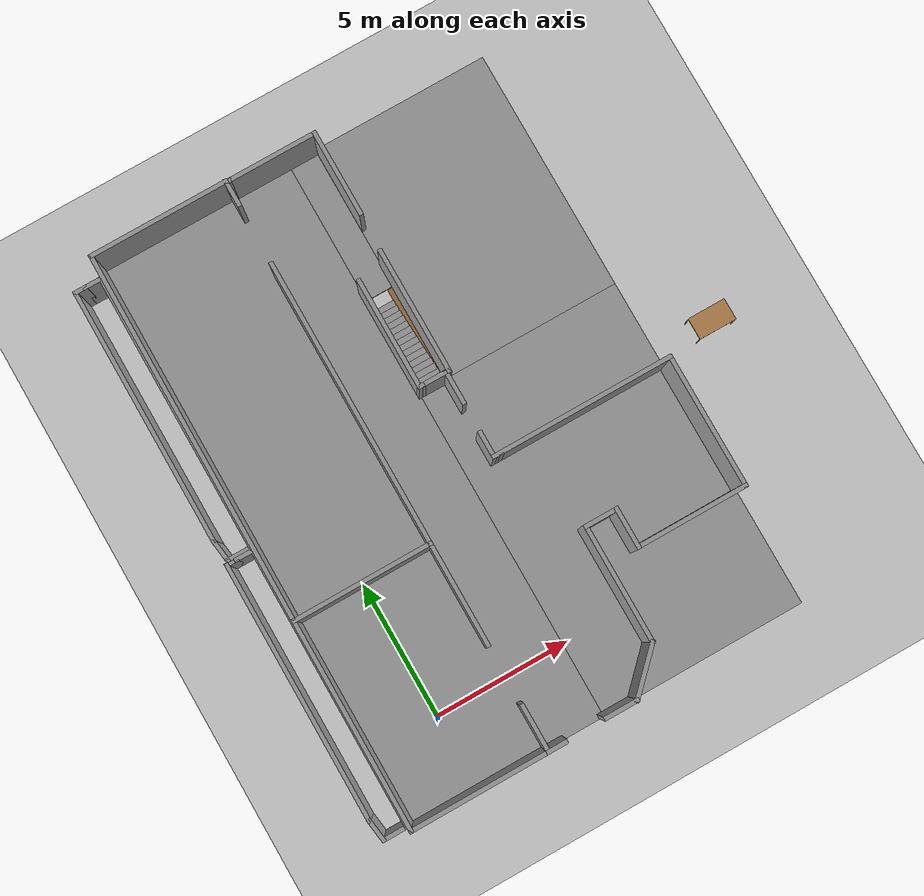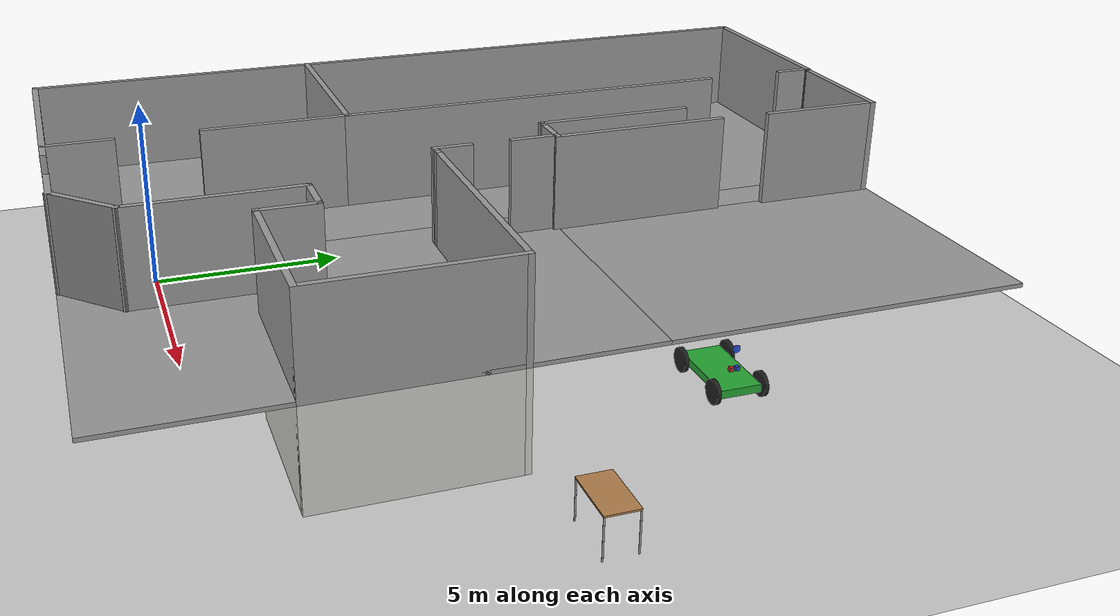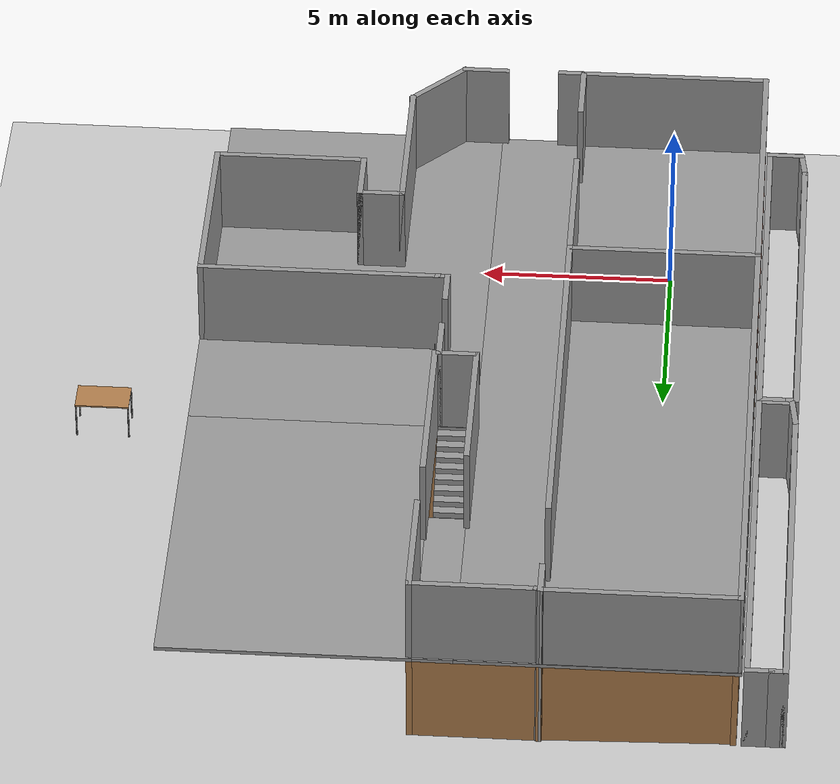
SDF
<sdf version="1.6">
 <world name="default">
  <light name="sun" type="directional">
   <pose>0 0 10 0 -0 0</pose>
   <diffuse>0.8 0.8 0.8 1</diffuse>
   <specular>0.1 0.1 0.1 1</specular>
   <attenuation>
    <range>1000</range>
    <constant>0.9</constant>
    <linear>0.01</linear>
    <quadratic>0.001</quadratic>
   </attenuation>
   <direction>-0.5 0.5 -1</direction>
  </light>
  <model name="ground_plane">
   <static>1</static>
   <link name="link">
    <collision name="collision">
     <geometry><plane><normal>0 0 1</normal><size>100 100</size></plane></geometry>
     <surface><friction><ode><mu>100</mu><mu2>50</mu2></ode></friction></surface>
    </collision>
    <visual name="visual">
     <cast_shadows>0</cast_shadows>
     <geometry><plane><normal>0 0 1</normal><size>100 100</size></plane></geometry>
     <material>
      <script><uri>file://media/materials/scripts/gazebo.material</uri><name>Gazebo/Grey</name></script>
     </material>
    </visual>
   </link>
  </model>
  <gravity>0 0 -9.8</gravity>
  <magnetic_field>6e-06 2.3e-05 -4.2e-05</magnetic_field>
  <atmosphere type="adiabatic"/>
  <physics name="default_physics" default="0" type="ode">
   <max_step_size>0.001</max_step_size>
   <real_time_factor>1</real_time_factor>
   <real_time_update_rate>1000</real_time_update_rate>
  </physics>
  <scene><ambient>0.4 0.4 0.4 1</ambient><background>0.7 0.7 0.7 1</background><shadows>1</shadows></scene>
  <spherical_coordinates>
   <surface_model>EARTH_WGS84</surface_model>
   <latitude_deg>0</latitude_deg>
   <longitude_deg>0</longitude_deg>
   <elevation>0</elevation>
   <heading_deg>0</heading_deg>
  </spherical_coordinates>
  <model name="RPL_Floor7_Sketch">
   <pose>4.78977 7.76362 0 0 -0 0</pose>
   <link name="Floor_0">
    <pose>0.000155 0 2.5 0 -0 0</pose>
    <visual name="Floor_0_Visual_0">
     <pose>-3.6687 0 0.05 0 -0 0</pose>
     <geometry><box><size>7.07279 20.6611 0.1</size></box></geometry>
     <material>
      <script><uri>file://media/materials/scripts/gazebo.material</uri><name>Gazebo/Grey</name></script>
      <ambient>1 1 1 1</ambient>
     </material>
    </visual>
    <collision name="Floor_0_Collision_0">
     <geometry><box><size>7.07279 20.6611 0.1</size></box></geometry>
     <pose>-3.6687 0 0.05 0 -0 0</pose>
    </collision>
    <visual name="Floor_0_Visual_1">
     <pose>3.53639 -4.35677 0.05 0 -0 0</pose>
     <geometry><box><size>7.3374 11.9476 0.1</size></box></geometry>
     <material>
      <script><uri>file://media/materials/scripts/gazebo.material</uri><name>Gazebo/Grey</name></script>
      <ambient>1 1 1 1</ambient>
     </material>
    </visual>
    <collision name="Floor_0_Collision_1">
     <geometry><box><size>7.3374 11.9476 0.1</size></box></geometry>
     <pose>3.53639 -4.35677 0.05 0 -0 0</pose>
    </collision>
    <visual name="Floor_0_Visual_2">
     <pose>4.03639 5.97379 0.05 0 -0 0</pose>
     <geometry><box><size>6.3374 8.71353 0.1</size></box></geometry>
     <material>
      <script><uri>file://media/materials/scripts/gazebo.material</uri><name>Gazebo/Grey</name></script>
      <ambient>1 1 1 1</ambient>
     </material>
    </visual>
    <collision name="Floor_0_Collision_2">
     <geometry><box><size>6.3374 8.71353 0.1</size></box></geometry>
     <pose>4.03639 5.97379 0.05 0 -0 0</pose>
    </collision>
    <visual name="Floor_0_Visual_3">
     <pose>0.367695 7.72379 0.05 0 -0 0</pose>
     <geometry><box><size>1 5.21353 0.1</size></box></geometry>
     <material>
      <script><uri>file://media/materials/scripts/gazebo.material</uri><name>Gazebo/Grey</name></script>
      <ambient>1 1 1 1</ambient>
     </material>
    </visual>
    <collision name="Floor_0_Collision_3">
     <geometry><box><size>1 5.21353 0.1</size></box></geometry>
     <pose>0.367695 7.72379 0.05 0 -0 0</pose>
    </collision>
   </link>
   <link name="Stairs_0">
    <visual name="Stairs_0_Visual_0">
     <pose>0.36785 5.00036 0.083333 0 -0 0</pose>
     <geometry><box><size>1 0.233333 0.166667</size></box></geometry>
     <material>
      <script><uri>file://media/materials/scripts/gazebo.material</uri><name>Gazebo/Grey</name></script>
      <ambient>1 1 1 1</ambient>
     </material>
    </visual>
    <collision name="Stairs_0_Collision_0">
     <geometry><box><size>1 0.233333 0.166667</size></box></geometry>
     <pose>0.36785 5.00036 0.083333 0 -0 0</pose>
    </collision>
    <visual name="Stairs_0_Visual_1">
     <pose>0.36785 4.76702 0.25 0 -0 0</pose>
     <geometry><box><size>1 0.233333 0.166667</size></box></geometry>
     <material>
      <script><uri>file://media/materials/scripts/gazebo.material</uri><name>Gazebo/Grey</name></script>
      <ambient>1 1 1 1</ambient>
     </material>
    </visual>
    <collision name="Stairs_0_Collision_1">
     <geometry><box><size>1 0.233333 0.166667</size></box></geometry>
     <pose>0.36785 4.76702 0.25 0 -0 0</pose>
    </collision>
    <visual name="Stairs_0_Visual_2">
     <pose>0.36785 4.53369 0.416667 0 -0 0</pose>
     <geometry><box><size>1 0.233333 0.166667</size></box></geometry>
     <material>
      <script><uri>file://media/materials/scripts/gazebo.material</uri><name>Gazebo/Grey</name></script>
      <ambient>1 1 1 1</ambient>
     </material>
    </visual>
    <collision name="Stairs_0_Collision_2">
     <geometry><box><size>1 0.233333 0.166667</size></box></geometry>
     <pose>0.36785 4.53369 0.416667 0 -0 0</pose>
    </collision>
    <visual name="Stairs_0_Visual_3">
     <pose>0.36785 4.30036 0.583333 0 -0 0</pose>
     <geometry><box><size>1 0.233333 0.166667</size></box></geometry>
     <material>
      <script><uri>file://media/materials/scripts/gazebo.material</uri><name>Gazebo/Grey</name></script>
      <ambient>1 1 1 1</ambient>
     </material>
    </visual>
    <collision name="Stairs_0_Collision_3">
     <geometry><box><size>1 0.233333 0.166667</size></box></geometry>
     <pose>0.36785 4.30036 0.583333 0 -0 0</pose>
    </collision>
    <visual name="Stairs_0_Visual_4">
     <pose>0.36785 4.06702 0.75 0 -0 0</pose>
     <geometry><box><size>1 0.233333 0.166667</size></box></geometry>
     <material>
      <script><uri>file://media/materials/scripts/gazebo.material</uri><name>Gazebo/Grey</name></script>
      <ambient>1 1 1 1</ambient>
     </material>
    </visual>
    <collision name="Stairs_0_Collision_4">
     <geometry><box><size>1 0.233333 0.166667</size></box></geometry>
     <pose>0.36785 4.06702 0.75 0 -0 0</pose>
    </collision>
    <visual name="Stairs_0_Visual_5">
     <pose>0.36785 3.83369 0.916667 0 -0 0</pose>
     <geometry><box><size>1 0.233333 0.166667</size></box></geometry>
     <material>
      <script><uri>file://media/materials/scripts/gazebo.material</uri><name>Gazebo/Grey</name></script>
      <ambient>1 1 1 1</ambient>
     </material>
    </visual>
    <collision name="Stairs_0_Collision_5">
     <geometry><box><size>1 0.233333 0.166667</size></box></geometry>
     <pose>0.36785 3.83369 0.916667 0 -0 0</pose>
    </collision>
    <visual name="Stairs_0_Visual_6">
     <pose>0.36785 3.60036 1.08333 0 -0 0</pose>
     <geometry><box><size>1 0.233333 0.166667</size></box></geometry>
     <material>
      <script><uri>file://media/materials/scripts/gazebo.material</uri><name>Gazebo/Grey</name></script>
      <ambient>1 1 1 1</ambient>
     </material>
    </visual>
    <collision name="Stairs_0_Collision_6">
     <geometry><box><size>1 0.233333 0.166667</size></box></geometry>
     <pose>0.36785 3.60036 1.08333 0 -0 0</pose>
    </collision>
    <visual name="Stairs_0_Visual_7">
     <pose>0.36785 3.36702 1.25 0 -0 0</pose>
     <geometry><box><size>1 0.233333 0.166667</size></box></geometry>
     <material>
      <script><uri>file://media/materials/scripts/gazebo.material</uri><name>Gazebo/Grey</name></script>
      <ambient>1 1 1 1</ambient>
     </material>
    </visual>
    <collision name="Stairs_0_Collision_7">
     <geometry><box><size>1 0.233333 0.166667</size></box></geometry>
     <pose>0.36785 3.36702 1.25 0 -0 0</pose>
    </collision>
    <visual name="Stairs_0_Visual_8">
     <pose>0.36785 3.13369 1.41667 0 -0 0</pose>
     <geometry><box><size>1 0.233333 0.166667</size></box></geometry>
     <material>
      <script><uri>file://media/materials/scripts/gazebo.material</uri><name>Gazebo/Grey</name></script>
      <ambient>1 1 1 1</ambient>
     </material>
    </visual>
    <collision name="Stairs_0_Collision_8">
     <geometry><box><size>1 0.233333 0.166667</size></box></geometry>
     <pose>0.36785 3.13369 1.41667 0 -0 0</pose>
    </collision>
    <visual name="Stairs_0_Visual_9">
     <pose>0.36785 2.90036 1.58333 0 -0 0</pose>
     <geometry><box><size>1 0.233333 0.166667</size></box></geometry>
     <material>
      <script><uri>file://media/materials/scripts/gazebo.material</uri><name>Gazebo/Grey</name></script>
      <ambient>1 1 1 1</ambient>
     </material>
    </visual>
    <collision name="Stairs_0_Collision_9">
     <geometry><box><size>1 0.233333 0.166667</size></box></geometry>
     <pose>0.36785 2.90036 1.58333 0 -0 0</pose>
    </collision>
    <visual name="Stairs_0_Visual_10">
     <pose>0.36785 2.66702 1.75 0 -0 0</pose>
     <geometry><box><size>1 0.233333 0.166667</size></box></geometry>
     <material>
      <script><uri>file://media/materials/scripts/gazebo.material</uri><name>Gazebo/Grey</name></script>
      <ambient>1 1 1 1</ambient>
     </material>
    </visual>
    <collision name="Stairs_0_Collision_10">
     <geometry><box><size>1 0.233333 0.166667</size></box></geometry>
     <pose>0.36785 2.66702 1.75 0 -0 0</pose>
    </collision>
    <visual name="Stairs_0_Visual_11">
     <pose>0.36785 2.43369 1.91667 0 -0 0</pose>
     <geometry><box><size>1 0.233333 0.166667</size></box></geometry>
     <material>
      <script><uri>file://media/materials/scripts/gazebo.material</uri><name>Gazebo/Grey</name></script>
      <ambient>1 1 1 1</ambient>
     </material>
    </visual>
    <collision name="Stairs_0_Collision_11">
     <geometry><box><size>1 0.233333 0.166667</size></box></geometry>
     <pose>0.36785 2.43369 1.91667 0 -0 0</pose>
    </collision>
    <visual name="Stairs_0_Visual_12">
     <pose>0.36785 2.20036 2.08333 0 -0 0</pose>
     <geometry><box><size>1 0.233333 0.166667</size></box></geometry>
     <material>
      <script><uri>file://media/materials/scripts/gazebo.material</uri><name>Gazebo/Grey</name></script>
      <ambient>1 1 1 1</ambient>
     </material>
    </visual>
    <collision name="Stairs_0_Collision_12">
     <geometry><box><size>1 0.233333 0.166667</size></box></geometry>
     <pose>0.36785 2.20036 2.08333 0 -0 0</pose>
    </collision>
    <visual name="Stairs_0_Visual_13">
     <pose>0.36785 1.96702 2.25 0 -0 0</pose>
     <geometry><box><size>1 0.233333 0.166667</size></box></geometry>
     <material>
      <script><uri>file://media/materials/scripts/gazebo.material</uri><name>Gazebo/Grey</name></script>
      <ambient>1 1 1 1</ambient>
     </material>
    </visual>
    <collision name="Stairs_0_Collision_13">
     <geometry><box><size>1 0.233333 0.166667</size></box></geometry>
     <pose>0.36785 1.96702 2.25 0 -0 0</pose>
    </collision>
    <visual name="Stairs_0_Visual_14">
     <pose>0.36785 1.73369 2.41667 0 -0 0</pose>
     <geometry><box><size>1 0.233333 0.166667</size></box></geometry>
     <material>
      <script><uri>file://media/materials/scripts/gazebo.material</uri><name>Gazebo/Grey</name></script>
      <ambient>1 1 1 1</ambient>
     </material>
    </visual>
    <collision name="Stairs_0_Collision_14">
     <geometry><box><size>1 0.233333 0.166667</size></box></geometry>
     <pose>0.36785 1.73369 2.41667 0 -0 0</pose>
    </collision>
   </link>
   <link name="Wall_0">
    <collision name="Wall_0_Collision">
     <geometry><box><size>5 0.15 2.5</size></box></geometry>
     <pose>0 0 1.25 0 -0 0</pose>
    </collision>
    <visual name="Wall_0_Visual">
     <pose>0 0 1.25 0 -0 0</pose>
     <geometry><box><size>5 0.15 2.5</size></box></geometry>
     <material>
      <script><uri>file://media/materials/scripts/gazebo.material</uri><name>Gazebo/Bricks</name></script>
      <ambient>1 1 1 1</ambient>
     </material>
    </visual>
    <pose>-4.70477 -2.89037 0 0 -0 3.14159</pose>
   </link>
   <link name="Wall_10">
    <collision name="Wall_10_Collision">
     <geometry><box><size>10.25 0.15 2.5</size></box></geometry>
     <pose>0 0 1.25 0 -0 0</pose>
    </collision>
    <visual name="Wall_10_Visual">
     <pose>0 0 1.25 0 -0 0</pose>
     <geometry><box><size>10.25 0.15 2.5</size></box></geometry>
     <material>
      <script><uri>file://media/materials/scripts/gazebo.material</uri><name>Gazebo/Wood</name></script>
      <ambient>1 1 1 1</ambient>
     </material>
    </visual>
    <pose>-2.27977 2.15963 0 0 -0 1.5708</pose>
   </link>
   <link name="Wall_12">
    <collision name="Wall_12_Collision">
     <geometry><box><size>0.75 0.15 2.5</size></box></geometry>
     <pose>0 0 1.25 0 -0 0</pose>
    </collision>
    <visual name="Wall_12_Visual">
     <pose>0 0 1.25 0 -0 0</pose>
     <geometry><box><size>0.75 0.15 2.5</size></box></geometry>
     <material>
      <script><uri>file://media/materials/scripts/gazebo.material</uri><name>Gazebo/Bricks</name></script>
      <ambient>1 1 1 1</ambient>
     </material>
    </visual>
    <pose>-1.97977 -10.2404 0 0 -0 0</pose>
   </link>
   <link name="Wall_22">
    <collision name="Wall_22_Collision">
     <geometry><box><size>1.25 0.15 2.5</size></box></geometry>
     <pose>0 0 1.25 0 -0 0</pose>
    </collision>
    <visual name="Wall_22_Visual">
     <pose>0 0 1.25 0 -0 0</pose>
     <geometry><box><size>1.25 0.15 2.5</size></box></geometry>
     <material>
      <script><uri>file://media/materials/scripts/gazebo.material</uri><name>Gazebo/CeilingTiled</name></script>
      <ambient>1 1 1 1</ambient>
     </material>
    </visual>
    <pose>0.322098 -10.2245 0 0 -0 0</pose>
   </link>
   <link name="Wall_23">
    <collision name="Wall_23_Collision">
     <geometry><box><size>2 0.15 2.5</size></box></geometry>
     <pose>0 0 1.25 0 -0 0</pose>
    </collision>
    <visual name="Wall_23_Visual">
     <pose>0 0 1.25 0 -0 0</pose>
     <geometry><box><size>2 0.15 2.5</size></box></geometry>
     <material>
      <script><uri>file://media/materials/scripts/gazebo.material</uri><name>Gazebo/CeilingTiled</name></script>
      <ambient>1 1 1 1</ambient>
     </material>
    </visual>
    <pose>1.52617 -9.57042 0 0 -0 0.785398</pose>
   </link>
   <link name="Wall_24">
    <collision name="Wall_24_Collision">
     <geometry><box><size>4.25 0.15 2.5</size></box></geometry>
     <pose>0 0 1.25 0 -0 0</pose>
    </collision>
    <visual name="Wall_24_Visual">
     <pose>0 0 1.25 0 -0 0</pose>
     <geometry><box><size>4.25 0.15 2.5</size></box></geometry>
     <material>
      <script><uri>file://media/materials/scripts/gazebo.material</uri><name>Gazebo/CeilingTiled</name></script>
      <ambient>1 1 1 1</ambient>
     </material>
    </visual>
    <pose>2.18025 -6.86634 0 0 -0 1.5708</pose>
   </link>
   <link name="Wall_25">
    <collision name="Wall_25_Collision">
     <geometry><box><size>1.25 0.15 2.5</size></box></geometry>
     <pose>0 0 1.25 0 -0 0</pose>
    </collision>
    <visual name="Wall_25_Visual">
     <pose>0 0 1.25 0 -0 0</pose>
     <geometry><box><size>1.25 0.15 2.5</size></box></geometry>
     <material>
      <script><uri>file://media/materials/scripts/gazebo.material</uri><name>Gazebo/CeilingTiled</name></script>
      <ambient>1 1 1 1</ambient>
     </material>
    </visual>
    <pose>2.73025 -4.81634 0 0 -0 0</pose>
   </link>
   <link name="Wall_26">
    <collision name="Wall_26_Collision">
     <geometry><box><size>1.5 0.15 2.5</size></box></geometry>
     <pose>0 0 1.25 0 -0 0</pose>
    </collision>
    <visual name="Wall_26_Visual">
     <pose>0 0 1.25 0 -0 0</pose>
     <geometry><box><size>1.5 0.15 2.5</size></box></geometry>
     <material>
      <script><uri>file://media/materials/scripts/gazebo.material</uri><name>Gazebo/CeilingTiled</name></script>
      <ambient>1 1 1 1</ambient>
     </material>
    </visual>
    <pose>3.28025 -5.49134 0 0 0 -1.5708</pose>
   </link>
   <link name="Wall_27">
    <collision name="Wall_27_Collision">
     <geometry><box><size>4 0.15 2.5</size></box></geometry>
     <pose>0 0 1.25 0 -0 0</pose>
    </collision>
    <visual name="Wall_27_Visual">
     <pose>0 0 1.25 0 -0 0</pose>
     <geometry><box><size>4 0.15 2.5</size></box></geometry>
     <material>
      <script><uri>file://media/materials/scripts/gazebo.material</uri><name>Gazebo/CeilingTiled</name></script>
      <ambient>1 1 1 1</ambient>
     </material>
    </visual>
    <pose>5.20524 -6.16634 0 0 -0 0</pose>
   </link>
   <link name="Wall_28">
    <collision name="Wall_28_Collision">
     <geometry><box><size>4.8032 0.15 2.5</size></box></geometry>
     <pose>0 0 1.25 0 -0 0</pose>
    </collision>
    <visual name="Wall_28_Visual">
     <pose>0 0 1.25 0 -0 0</pose>
     <geometry><box><size>4.8032 0.15 2.5</size></box></geometry>
     <material>
      <script><uri>file://media/materials/scripts/gazebo.material</uri><name>Gazebo/CeilingTiled</name></script>
      <ambient>1 1 1 1</ambient>
     </material>
    </visual>
    <pose>7.13025 -3.83974 0 0 -0 1.5708</pose>
   </link>
   <link name="Wall_30">
    <collision name="Wall_30_Collision">
     <geometry><box><size>0.15 0.15 2.5</size></box></geometry>
     <pose>0 0 1.25 0 -0 0</pose>
    </collision>
    <visual name="Wall_30_Visual">
     <pose>0 0 1.25 0 -0 0</pose>
     <geometry><box><size>0.15 0.15 2.5</size></box></geometry>
     <material>
      <script><uri>file://media/materials/scripts/gazebo.material</uri><name>Gazebo/Grey</name></script>
      <ambient>1 1 1 1</ambient>
     </material>
    </visual>
    <pose>1.03025 -1.51314 0 0 -0 0</pose>
   </link>
   <link name="Wall_31">
    <collision name="Wall_31_Collision">
     <geometry><box><size>0.15 0.15 2.5</size></box></geometry>
     <pose>0 0 1.25 0 -0 0</pose>
    </collision>
    <visual name="Wall_31_Visual">
     <pose>0 0 1.25 0 -0 0</pose>
     <geometry><box><size>0.15 0.15 2.5</size></box></geometry>
     <material>
      <script><uri>file://media/materials/scripts/gazebo.material</uri><name>Gazebo/Grey</name></script>
      <ambient>1 1 1 1</ambient>
     </material>
    </visual>
    <pose>1.03025 -1.51314 0 0 -0 0</pose>
   </link>
   <link name="Wall_34">
    <collision name="Wall_34_Collision">
     <geometry><box><size>6.5 0.15 2.5</size></box></geometry>
     <pose>0 0 1.25 0 -0 0</pose>
    </collision>
    <visual name="Wall_34_Visual">
     <pose>0 0 1.25 0 -0 0</pose>
     <geometry><box><size>6.5 0.15 2.5</size></box></geometry>
     <material>
      <script><uri>file://media/materials/scripts/gazebo.material</uri><name>Gazebo/CeilingTiled</name></script>
      <ambient>1 1 1 1</ambient>
     </material>
    </visual>
    <pose>3.95525 -1.51314 0 0 -0 3.14159</pose>
   </link>
   <link name="Wall_35">
    <collision name="Wall_35_Collision">
     <geometry><box><size>1 0.15 2.5</size></box></geometry>
     <pose>0 0 1.25 0 -0 0</pose>
    </collision>
    <visual name="Wall_35_Visual">
     <pose>0 0 1.25 0 -0 0</pose>
     <geometry><box><size>1 0.15 2.5</size></box></geometry>
     <material>
      <script><uri>file://media/materials/scripts/gazebo.material</uri><name>Gazebo/Wood</name></script>
      <ambient>1 1 1 1</ambient>
     </material>
    </visual>
    <pose>0.780246 -1.08814 0 0 -0 1.5708</pose>
   </link>
   <link name="Wall_37">
    <collision name="Wall_37_Collision">
     <geometry><box><size>1.25 0.15 2.5</size></box></geometry>
     <pose>0 0 1.25 0 -0 0</pose>
    </collision>
    <visual name="Wall_37_Visual">
     <pose>0 0 1.25 0 -0 0</pose>
     <geometry><box><size>1.25 0.15 2.5</size></box></geometry>
     <material>
      <script><uri>file://media/materials/scripts/gazebo.material</uri><name>Gazebo/Wood</name></script>
      <ambient>1 1 1 1</ambient>
     </material>
    </visual>
    <pose>0.796113 0.980362 0 0 -0 1.5708</pose>
   </link>
   <link name="Wall_38">
    <collision name="Wall_38_Collision">
     <geometry><box><size>1 0.15 2.5</size></box></geometry>
     <pose>0 0 1.25 0 -0 0</pose>
    </collision>
    <visual name="Wall_38_Visual">
     <pose>0 0 1.25 0 -0 0</pose>
     <geometry><box><size>1 0.15 2.5</size></box></geometry>
     <material>
      <script><uri>file://media/materials/scripts/gazebo.material</uri><name>Gazebo/Wood</name></script>
      <ambient>1 1 1 1</ambient>
     </material>
    </visual>
    <pose>0.371113 1.53036 0 0 -0 3.14159</pose>
   </link>
   <link name="Wall_4">
    <pose>-7.12977 -6.56537 0 0 0 -1.5708</pose>
    <visual name="Wall_4_Visual_0">
     <pose>-3.45071 0 1.25 0 -0 0</pose>
     <geometry><box><size>0.598591 0.15 2.5</size></box></geometry>
     <material>
      <script><uri>file://media/materials/scripts/gazebo.material</uri><name>Gazebo/Bricks</name></script>
      <ambient>1 1 1 1</ambient>
     </material>
    </visual>
    <collision name="Wall_4_Collision_0">
     <geometry><box><size>0.598591 0.15 2.5</size></box></geometry>
     <pose>-3.45071 0 1.25 0 -0 0</pose>
    </collision>
    <visual name="Wall_4_Visual_1">
     <pose>0.299295 0 0.25 0 -0 0</pose>
     <geometry><box><size>6.90141 0.15 0.5</size></box></geometry>
     <material>
      <script><uri>file://media/materials/scripts/gazebo.material</uri><name>Gazebo/Bricks</name></script>
      <ambient>1 1 1 1</ambient>
     </material>
    </visual>
    <collision name="Wall_4_Collision_1">
     <geometry><box><size>6.90141 0.15 0.5</size></box></geometry>
     <pose>0.299295 0 0.25 0 -0 0</pose>
    </collision>
    <visual name="Wall_4_Visual_2">
     <pose>-1.83624 0 1.5 0 -0 0</pose>
     <geometry><box><size>1.03034 0.15 2</size></box></geometry>
     <material>
      <script><uri>file://media/materials/scripts/gazebo.material</uri><name>Gazebo/Bricks</name></script>
      <ambient>1 1 1 1</ambient>
     </material>
    </visual>
    <collision name="Wall_4_Collision_2">
     <geometry><box><size>1.03034 0.15 2</size></box></geometry>
     <pose>-1.83624 0 1.5 0 -0 0</pose>
    </collision>
    <visual name="Wall_4_Visual_3">
     <pose>-0.056191 0 1.5 0 -0 0</pose>
     <geometry><box><size>0.929767 0.15 2</size></box></geometry>
     <material>
      <script><uri>file://media/materials/scripts/gazebo.material</uri><name>Gazebo/Bricks</name></script>
      <ambient>1 1 1 1</ambient>
     </material>
    </visual>
    <collision name="Wall_4_Collision_3">
     <geometry><box><size>0.929767 0.15 2</size></box></geometry>
     <pose>-0.056191 0 1.5 0 -0 0</pose>
    </collision>
    <visual name="Wall_4_Visual_4">
     <pose>1.70375 0 1.5 0 -0 0</pose>
     <geometry><box><size>0.990108 0.15 2</size></box></geometry>
     <material>
      <script><uri>file://media/materials/scripts/gazebo.material</uri><name>Gazebo/Bricks</name></script>
      <ambient>1 1 1 1</ambient>
     </material>
    </visual>
    <collision name="Wall_4_Collision_4">
     <geometry><box><size>0.990108 0.15 2</size></box></geometry>
     <pose>1.70375 0 1.5 0 -0 0</pose>
    </collision>
    <visual name="Wall_4_Visual_5">
     <pose>3.3744 0 1.5 0 -0 0</pose>
     <geometry><box><size>0.751199 0.15 2</size></box></geometry>
     <material>
      <script><uri>file://media/materials/scripts/gazebo.material</uri><name>Gazebo/Bricks</name></script>
      <ambient>1 1 1 1</ambient>
     </material>
    </visual>
    <collision name="Wall_4_Collision_5">
     <geometry><box><size>0.751199 0.15 2</size></box></geometry>
     <pose>3.3744 0 1.5 0 -0 0</pose>
    </collision>
    <visual name="Wall_4_Visual_6">
     <pose>-2.75141 0 1.9 0 -0 0</pose>
     <geometry><box><size>0.8 0.15 1.2</size></box></geometry>
     <material>
      <script><uri>file://media/materials/scripts/gazebo.material</uri><name>Gazebo/Bricks</name></script>
      <ambient>1 1 1 1</ambient>
     </material>
    </visual>
    <collision name="Wall_4_Collision_6">
     <geometry><box><size>0.8 0.15 1.2</size></box></geometry>
     <pose>-2.75141 0 1.9 0 -0 0</pose>
    </collision>
    <visual name="Wall_4_Visual_7">
     <pose>-0.921074 0 1.9 0 -0 0</pose>
     <geometry><box><size>0.8 0.15 1.2</size></box></geometry>
     <material>
      <script><uri>file://media/materials/scripts/gazebo.material</uri><name>Gazebo/Bricks</name></script>
      <ambient>1 1 1 1</ambient>
     </material>
    </visual>
    <collision name="Wall_4_Collision_7">
     <geometry><box><size>0.8 0.15 1.2</size></box></geometry>
     <pose>-0.921074 0 1.9 0 -0 0</pose>
    </collision>
    <visual name="Wall_4_Visual_8">
     <pose>0.808693 0 1.9 0 -0 0</pose>
     <geometry><box><size>0.8 0.15 1.2</size></box></geometry>
     <material>
      <script><uri>file://media/materials/scripts/gazebo.material</uri><name>Gazebo/Bricks</name></script>
      <ambient>1 1 1 1</ambient>
     </material>
    </visual>
    <collision name="Wall_4_Collision_8">
     <geometry><box><size>0.8 0.15 1.2</size></box></geometry>
     <pose>0.808693 0 1.9 0 -0 0</pose>
    </collision>
    <visual name="Wall_4_Visual_9">
     <pose>2.5988 0 1.9 0 -0 0</pose>
     <geometry><box><size>0.8 0.15 1.2</size></box></geometry>
     <material>
      <script><uri>file://media/materials/scripts/gazebo.material</uri><name>Gazebo/Bricks</name></script>
      <ambient>1 1 1 1</ambient>
     </material>
    </visual>
    <collision name="Wall_4_Collision_9">
     <geometry><box><size>0.8 0.15 1.2</size></box></geometry>
     <pose>2.5988 0 1.9 0 -0 0</pose>
    </collision>
   </link>
   <link name="Wall_42">
    <collision name="Wall_42_Collision">
     <geometry><box><size>0.25 0.15 2.5</size></box></geometry>
     <pose>0 0 1.25 0 -0 0</pose>
    </collision>
    <visual name="Wall_42_Visual">
     <pose>0 0 1.25 0 -0 0</pose>
     <geometry><box><size>0.25 0.15 2.5</size></box></geometry>
     <material>
      <script><uri>file://media/materials/scripts/gazebo.material</uri><name>Gazebo/Grey</name></script>
      <ambient>1 1 1 1</ambient>
     </material>
    </visual>
    <pose>-0.103887 1.53036 0 0 -0 3.14159</pose>
   </link>
   <link name="Wall_43">
    <collision name="Wall_43_Collision">
     <geometry><box><size>4 0.15 2.5</size></box></geometry>
     <pose>0 0 1.25 0 -0 0</pose>
    </collision>
    <visual name="Wall_43_Visual">
     <pose>0 0 1.25 0 -0 0</pose>
     <geometry><box><size>4 0.15 2.5</size></box></geometry>
     <material>
      <script><uri>file://media/materials/scripts/gazebo.material</uri><name>Gazebo/Wood</name></script>
      <ambient>1 1 1 1</ambient>
     </material>
    </visual>
    <pose>-0.153887 3.45536 0 0 -0 1.5708</pose>
   </link>
   <link name="Wall_45">
    <collision name="Wall_45_Collision">
     <geometry><box><size>0.25 0.15 2.5</size></box></geometry>
     <pose>0 0 1.25 0 -0 0</pose>
    </collision>
    <visual name="Wall_45_Visual">
     <pose>0 0 1.25 0 -0 0</pose>
     <geometry><box><size>0.25 0.15 2.5</size></box></geometry>
     <material>
      <script><uri>file://media/materials/scripts/gazebo.material</uri><name>Gazebo/Grey</name></script>
      <ambient>1 1 1 1</ambient>
     </material>
    </visual>
    <pose>0.846114 1.53036 0 0 -0 0</pose>
   </link>
   <link name="Wall_46">
    <collision name="Wall_46_Collision">
     <geometry><box><size>4.5 0.15 2.5</size></box></geometry>
     <pose>0 0 1.25 0 -0 0</pose>
    </collision>
    <visual name="Wall_46_Visual">
     <pose>0 0 1.25 0 -0 0</pose>
     <geometry><box><size>4.5 0.15 2.5</size></box></geometry>
     <material>
      <script><uri>file://media/materials/scripts/gazebo.material</uri><name>Gazebo/Wood</name></script>
      <ambient>1 1 1 1</ambient>
     </material>
    </visual>
    <pose>0.896113 3.70536 0 0 -0 1.5708</pose>
   </link>
   <link name="Wall_48">
    <collision name="Wall_48_Collision">
     <geometry><box><size>3.10701 0.15 2.5</size></box></geometry>
     <pose>0 0 1.25 0 -0 0</pose>
    </collision>
    <visual name="Wall_48_Visual">
     <pose>0 0 1.25 0 -0 0</pose>
     <geometry><box><size>3.10701 0.15 2.5</size></box></geometry>
     <material>
      <script><uri>file://media/materials/scripts/gazebo.material</uri><name>Gazebo/Wood</name></script>
      <ambient>1 1 1 1</ambient>
     </material>
    </visual>
    <pose>0.946638 8.73432 0 0 -0 1.5708</pose>
   </link>
   <link name="Wall_5">
    <collision name="Wall_5_Collision">
     <geometry><box><size>5 0.15 2.5</size></box></geometry>
     <pose>0 0 1.25 0 -0 0</pose>
    </collision>
    <visual name="Wall_5_Visual">
     <pose>0 0 1.25 0 -0 0</pose>
     <geometry><box><size>5 0.15 2.5</size></box></geometry>
     <material>
      <script><uri>file://media/materials/scripts/gazebo.material</uri><name>Gazebo/Bricks</name></script>
      <ambient>1 1 1 1</ambient>
     </material>
    </visual>
    <pose>-4.70477 -10.2404 0 0 -0 0</pose>
   </link>
   <link name="Wall_56">
    <collision name="Wall_56_Collision">
     <geometry><box><size>3.25 0.15 2.5</size></box></geometry>
     <pose>0 0 1.25 0 -0 0</pose>
    </collision>
    <visual name="Wall_56_Visual">
     <pose>0 0 1.25 0 -0 0</pose>
     <geometry><box><size>3.25 0.15 2.5</size></box></geometry>
     <material>
      <script><uri>file://media/materials/scripts/gazebo.material</uri><name>Gazebo/Wood</name></script>
      <ambient>1 1 1 1</ambient>
     </material>
    </visual>
    <pose>-0.603362 10.2128 0 0 -0 3.14159</pose>
   </link>
   <link name="Wall_57">
    <collision name="Wall_57_Collision">
     <geometry><box><size>0.25 0.15 2.5</size></box></geometry>
     <pose>0 0 1.25 0 -0 0</pose>
    </collision>
    <visual name="Wall_57_Visual">
     <pose>0 0 1.25 0 -0 0</pose>
     <geometry><box><size>0.25 0.15 2.5</size></box></geometry>
     <material>
      <script><uri>file://media/materials/scripts/gazebo.material</uri><name>Gazebo/Grey</name></script>
      <ambient>1 1 1 1</ambient>
     </material>
    </visual>
    <pose>-2.20166 10.2258 0 0 -0 2.87979</pose>
   </link>
   <link name="Wall_58">
    <collision name="Wall_58_Collision">
     <geometry><box><size>0.946497 0.15 2.5</size></box></geometry>
     <pose>0 0 1.25 0 -0 0</pose>
    </collision>
    <visual name="Wall_58_Visual">
     <pose>0 0 1.25 0 -0 0</pose>
     <geometry><box><size>0.946497 0.15 2.5</size></box></geometry>
     <material>
      <script><uri>file://media/materials/scripts/gazebo.material</uri><name>Gazebo/Wood</name></script>
      <ambient>1 1 1 1</ambient>
     </material>
    </visual>
    <pose>-2.24995 9.84045 0 0 0 -1.5708</pose>
   </link>
   <link name="Wall_6">
    <collision name="Wall_6_Collision">
     <geometry><box><size>1.75 0.15 2.5</size></box></geometry>
     <pose>0 0 1.25 0 -0 0</pose>
    </collision>
    <visual name="Wall_6_Visual">
     <pose>0 0 1.25 0 -0 0</pose>
     <geometry><box><size>1.75 0.15 2.5</size></box></geometry>
     <material>
      <script><uri>file://media/materials/scripts/gazebo.material</uri><name>Gazebo/Bricks</name></script>
      <ambient>1 1 1 1</ambient>
     </material>
    </visual>
    <pose>-2.27977 -9.44037 0 0 -0 1.5708</pose>
   </link>
   <link name="Wall_60">
    <collision name="Wall_60_Collision">
     <geometry><box><size>4.94918 0.15 2.5</size></box></geometry>
     <pose>0 0 1.25 0 -0 0</pose>
    </collision>
    <visual name="Wall_60_Visual">
     <pose>0 0 1.25 0 -0 0</pose>
     <geometry><box><size>4.94918 0.15 2.5</size></box></geometry>
     <material>
      <script><uri>file://media/materials/scripts/gazebo.material</uri><name>Gazebo/Wood</name></script>
      <ambient>1 1 1 1</ambient>
     </material>
    </visual>
    <pose>-4.6482 10.1049 0 0 0 -3.10814</pose>
   </link>
   <link name="Wall_61">
    <pose>-7.08811 3.59391 0 0 0 -1.57722</pose>
    <visual name="Wall_61_Visual_0">
     <pose>-6.15402 0 1.25 0 -0 0</pose>
     <geometry><box><size>0.810784 0.15 2.5</size></box></geometry>
     <material>
      <script><uri>file://media/materials/scripts/gazebo.material</uri><name>Gazebo/Wood</name></script>
      <ambient>1 1 1 1</ambient>
     </material>
    </visual>
    <collision name="Wall_61_Collision_0">
     <geometry><box><size>0.810784 0.15 2.5</size></box></geometry>
     <pose>-6.15402 0 1.25 0 -0 0</pose>
    </collision>
    <visual name="Wall_61_Visual_1">
     <pose>0.405392 0 0.25 0 -0 0</pose>
     <geometry><box><size>12.308 0.15 0.5</size></box></geometry>
     <material>
      <script><uri>file://media/materials/scripts/gazebo.material</uri><name>Gazebo/Wood</name></script>
      <ambient>1 1 1 1</ambient>
     </material>
    </visual>
    <collision name="Wall_61_Collision_1">
     <geometry><box><size>12.308 0.15 0.5</size></box></geometry>
     <pose>0.405392 0 0.25 0 -0 0</pose>
    </collision>
    <visual name="Wall_61_Visual_2">
     <pose>-4.31789 0 1.5 0 -0 0</pose>
     <geometry><box><size>1.26148 0.15 2</size></box></geometry>
     <material>
      <script><uri>file://media/materials/scripts/gazebo.material</uri><name>Gazebo/Wood</name></script>
      <ambient>1 1 1 1</ambient>
     </material>
    </visual>
    <collision name="Wall_61_Collision_2">
     <geometry><box><size>1.26148 0.15 2</size></box></geometry>
     <pose>-4.31789 0 1.5 0 -0 0</pose>
    </collision>
    <visual name="Wall_61_Visual_3">
     <pose>-2.2832 0 1.5 0 -0 0</pose>
     <geometry><box><size>1.20791 0.15 2</size></box></geometry>
     <material>
      <script><uri>file://media/materials/scripts/gazebo.material</uri><name>Gazebo/Wood</name></script>
      <ambient>1 1 1 1</ambient>
     </material>
    </visual>
    <collision name="Wall_61_Collision_3">
     <geometry><box><size>1.20791 0.15 2</size></box></geometry>
     <pose>-2.2832 0 1.5 0 -0 0</pose>
    </collision>
    <visual name="Wall_61_Visual_4">
     <pose>-0.301468 0 1.5 0 -0 0</pose>
     <geometry><box><size>1.15554 0.15 2</size></box></geometry>
     <material>
      <script><uri>file://media/materials/scripts/gazebo.material</uri><name>Gazebo/Wood</name></script>
      <ambient>1 1 1 1</ambient>
     </material>
    </visual>
    <collision name="Wall_61_Collision_4">
     <geometry><box><size>1.15554 0.15 2</size></box></geometry>
     <pose>-0.301468 0 1.5 0 -0 0</pose>
    </collision>
    <visual name="Wall_61_Visual_5">
     <pose>1.75977 0 1.5 0 -0 0</pose>
     <geometry><box><size>1.36694 0.15 2</size></box></geometry>
     <material>
      <script><uri>file://media/materials/scripts/gazebo.material</uri><name>Gazebo/Wood</name></script>
      <ambient>1 1 1 1</ambient>
     </material>
    </visual>
    <collision name="Wall_61_Collision_5">
     <geometry><box><size>1.36694 0.15 2</size></box></geometry>
     <pose>1.75977 0 1.5 0 -0 0</pose>
    </collision>
    <visual name="Wall_61_Visual_6">
     <pose>4.00574 0 1.5 0 -0 0</pose>
     <geometry><box><size>1.52501 0.15 2</size></box></geometry>
     <material>
      <script><uri>file://media/materials/scripts/gazebo.material</uri><name>Gazebo/Wood</name></script>
      <ambient>1 1 1 1</ambient>
     </material>
    </visual>
    <collision name="Wall_61_Collision_6">
     <geometry><box><size>1.52501 0.15 2</size></box></geometry>
     <pose>4.00574 0 1.5 0 -0 0</pose>
    </collision>
    <visual name="Wall_61_Visual_7">
     <pose>6.06383 0 1.5 0 -0 0</pose>
     <geometry><box><size>0.991168 0.15 2</size></box></geometry>
     <material>
      <script><uri>file://media/materials/scripts/gazebo.material</uri><name>Gazebo/Wood</name></script>
      <ambient>1 1 1 1</ambient>
     </material>
    </visual>
    <collision name="Wall_61_Collision_7">
     <geometry><box><size>0.991168 0.15 2</size></box></geometry>
     <pose>6.06383 0 1.5 0 -0 0</pose>
    </collision>
    <visual name="Wall_61_Visual_8">
     <pose>-5.34863 0 1.9 0 -0 0</pose>
     <geometry><box><size>0.8 0.15 1.2</size></box></geometry>
     <material>
      <script><uri>file://media/materials/scripts/gazebo.material</uri><name>Gazebo/Wood</name></script>
      <ambient>1 1 1 1</ambient>
     </material>
    </visual>
    <collision name="Wall_61_Collision_8">
     <geometry><box><size>0.8 0.15 1.2</size></box></geometry>
     <pose>-5.34863 0 1.9 0 -0 0</pose>
    </collision>
    <visual name="Wall_61_Visual_9">
     <pose>-3.28715 0 1.9 0 -0 0</pose>
     <geometry><box><size>0.8 0.15 1.2</size></box></geometry>
     <material>
      <script><uri>file://media/materials/scripts/gazebo.material</uri><name>Gazebo/Wood</name></script>
      <ambient>1 1 1 1</ambient>
     </material>
    </visual>
    <collision name="Wall_61_Collision_9">
     <geometry><box><size>0.8 0.15 1.2</size></box></geometry>
     <pose>-3.28715 0 1.9 0 -0 0</pose>
    </collision>
    <visual name="Wall_61_Visual_10">
     <pose>-1.27924 0 1.9 0 -0 0</pose>
     <geometry><box><size>0.8 0.15 1.2</size></box></geometry>
     <material>
      <script><uri>file://media/materials/scripts/gazebo.material</uri><name>Gazebo/Wood</name></script>
      <ambient>1 1 1 1</ambient>
     </material>
    </visual>
    <collision name="Wall_61_Collision_10">
     <geometry><box><size>0.8 0.15 1.2</size></box></geometry>
     <pose>-1.27924 0 1.9 0 -0 0</pose>
    </collision>
    <visual name="Wall_61_Visual_11">
     <pose>0.676303 0 1.9 0 -0 0</pose>
     <geometry><box><size>0.8 0.15 1.2</size></box></geometry>
     <material>
      <script><uri>file://media/materials/scripts/gazebo.material</uri><name>Gazebo/Wood</name></script>
      <ambient>1 1 1 1</ambient>
     </material>
    </visual>
    <collision name="Wall_61_Collision_11">
     <geometry><box><size>0.8 0.15 1.2</size></box></geometry>
     <pose>0.676303 0 1.9 0 -0 0</pose>
    </collision>
    <visual name="Wall_61_Visual_12">
     <pose>2.84324 0 1.9 0 -0 0</pose>
     <geometry><box><size>0.8 0.15 1.2</size></box></geometry>
     <material>
      <script><uri>file://media/materials/scripts/gazebo.material</uri><name>Gazebo/Wood</name></script>
      <ambient>1 1 1 1</ambient>
     </material>
    </visual>
    <collision name="Wall_61_Collision_12">
     <geometry><box><size>0.8 0.15 1.2</size></box></geometry>
     <pose>2.84324 0 1.9 0 -0 0</pose>
    </collision>
    <visual name="Wall_61_Visual_13">
     <pose>5.16825 0 1.9 0 -0 0</pose>
     <geometry><box><size>0.8 0.15 1.2</size></box></geometry>
     <material>
      <script><uri>file://media/materials/scripts/gazebo.material</uri><name>Gazebo/Wood</name></script>
      <ambient>1 1 1 1</ambient>
     </material>
    </visual>
    <collision name="Wall_61_Collision_13">
     <geometry><box><size>0.8 0.15 1.2</size></box></geometry>
     <pose>5.16825 0 1.9 0 -0 0</pose>
    </collision>
   </link>
   <link name="Wall_63">
    <collision name="Wall_63_Collision">
     <geometry><box><size>5 0.15 2.5</size></box></geometry>
     <pose>0 0 1.25 0 -0 0</pose>
    </collision>
    <visual name="Wall_63_Visual">
     <pose>0 0 1.25 0 -0 0</pose>
     <geometry><box><size>5 0.15 2.5</size></box></geometry>
     <material>
      <script><uri>file://media/materials/scripts/gazebo.material</uri><name>Gazebo/Grey</name></script>
      <ambient>1 1 1 1</ambient>
     </material>
    </visual>
    <pose>-4.70477 -2.89037 2.5 0 -0 3.14159</pose>
   </link>
   <link name="Wall_64">
    <collision name="Wall_64_Collision">
     <geometry><box><size>7.5 0.15 2.5</size></box></geometry>
     <pose>0 0 1.25 0 -0 0</pose>
    </collision>
    <visual name="Wall_64_Visual">
     <pose>0 0 1.25 0 -0 0</pose>
     <geometry><box><size>7.5 0.15 2.5</size></box></geometry>
     <material>
      <script><uri>file://media/materials/scripts/gazebo.material</uri><name>Gazebo/Grey</name></script>
      <ambient>1 1 1 1</ambient>
     </material>
    </visual>
    <pose>-7.12977 -6.56537 2.5 0 0 -1.5708</pose>
   </link>
   <link name="Wall_65">
    <collision name="Wall_65_Collision">
     <geometry><box><size>5 0.15 2.5</size></box></geometry>
     <pose>0 0 1.25 0 -0 0</pose>
    </collision>
    <visual name="Wall_65_Visual">
     <pose>0 0 1.25 0 -0 0</pose>
     <geometry><box><size>5 0.15 2.5</size></box></geometry>
     <material>
      <script><uri>file://media/materials/scripts/gazebo.material</uri><name>Gazebo/Grey</name></script>
      <ambient>1 1 1 1</ambient>
     </material>
    </visual>
    <pose>-4.70477 -10.2404 2.5 0 -0 0</pose>
   </link>
   <link name="Wall_66">
    <collision name="Wall_66_Collision">
     <geometry><box><size>1.75 0.15 2.5</size></box></geometry>
     <pose>0 0 1.25 0 -0 0</pose>
    </collision>
    <visual name="Wall_66_Visual">
     <pose>0 0 1.25 0 -0 0</pose>
     <geometry><box><size>1.75 0.15 2.5</size></box></geometry>
     <material>
      <script><uri>file://media/materials/scripts/gazebo.material</uri><name>Gazebo/Grey</name></script>
      <ambient>1 1 1 1</ambient>
     </material>
    </visual>
    <pose>-2.27977 -9.44037 2.5 0 -0 1.5708</pose>
   </link>
   <link name="Wall_67">
    <collision name="Wall_67_Collision">
     <geometry><box><size>3.75 0.15 2.5</size></box></geometry>
     <pose>0 0 1.25 0 -0 0</pose>
    </collision>
    <visual name="Wall_67_Visual">
     <pose>0 0 1.25 0 -0 0</pose>
     <geometry><box><size>3.75 0.15 2.5</size></box></geometry>
     <material>
      <script><uri>file://media/materials/scripts/gazebo.material</uri><name>Gazebo/Grey</name></script>
      <ambient>1 1 1 1</ambient>
     </material>
    </visual>
    <pose>-2.27977 -4.69037 2.5 0 0 -1.5708</pose>
   </link>
   <link name="Wall_68">
    <collision name="Wall_68_Collision">
     <geometry><box><size>10.25 0.15 2.5</size></box></geometry>
     <pose>0 0 1.25 0 -0 0</pose>
    </collision>
    <visual name="Wall_68_Visual">
     <pose>0 0 1.25 0 -0 0</pose>
     <geometry><box><size>10.25 0.15 2.5</size></box></geometry>
     <material>
      <script><uri>file://media/materials/scripts/gazebo.material</uri><name>Gazebo/Grey</name></script>
      <ambient>1 1 1 1</ambient>
     </material>
    </visual>
    <pose>-2.27977 2.15963 2.5 0 -0 1.5708</pose>
   </link>
   <link name="Wall_69">
    <collision name="Wall_69_Collision">
     <geometry><box><size>0.75 0.15 2.5</size></box></geometry>
     <pose>0 0 1.25 0 -0 0</pose>
    </collision>
    <visual name="Wall_69_Visual">
     <pose>0 0 1.25 0 -0 0</pose>
     <geometry><box><size>0.75 0.15 2.5</size></box></geometry>
     <material>
      <script><uri>file://media/materials/scripts/gazebo.material</uri><name>Gazebo/Grey</name></script>
      <ambient>1 1 1 1</ambient>
     </material>
    </visual>
    <pose>-1.97977 -10.2404 2.5 0 -0 0</pose>
   </link>
   <link name="Wall_70">
    <collision name="Wall_70_Collision">
     <geometry><box><size>1.25 0.15 2.5</size></box></geometry>
     <pose>0 0 1.25 0 -0 0</pose>
    </collision>
    <visual name="Wall_70_Visual">
     <pose>0 0 1.25 0 -0 0</pose>
     <geometry><box><size>1.25 0.15 2.5</size></box></geometry>
     <material>
      <script><uri>file://media/materials/scripts/gazebo.material</uri><name>Gazebo/Grey</name></script>
      <ambient>1 1 1 1</ambient>
     </material>
    </visual>
    <pose>0.322098 -10.2245 2.5 0 -0 0</pose>
   </link>
   <link name="Wall_71">
    <collision name="Wall_71_Collision">
     <geometry><box><size>2 0.15 2.5</size></box></geometry>
     <pose>0 0 1.25 0 -0 0</pose>
    </collision>
    <visual name="Wall_71_Visual">
     <pose>0 0 1.25 0 -0 0</pose>
     <geometry><box><size>2 0.15 2.5</size></box></geometry>
     <material>
      <script><uri>file://media/materials/scripts/gazebo.material</uri><name>Gazebo/Grey</name></script>
      <ambient>1 1 1 1</ambient>
     </material>
    </visual>
    <pose>1.52617 -9.57042 2.5 0 -0 0.785398</pose>
   </link>
   <link name="Wall_72">
    <collision name="Wall_72_Collision">
     <geometry><box><size>4.25 0.15 2.5</size></box></geometry>
     <pose>0 0 1.25 0 -0 0</pose>
    </collision>
    <visual name="Wall_72_Visual">
     <pose>0 0 1.25 0 -0 0</pose>
     <geometry><box><size>4.25 0.15 2.5</size></box></geometry>
     <material>
      <script><uri>file://media/materials/scripts/gazebo.material</uri><name>Gazebo/Grey</name></script>
      <ambient>1 1 1 1</ambient>
     </material>
    </visual>
    <pose>2.18025 -6.86634 2.5 0 -0 1.5708</pose>
   </link>
   <link name="Wall_73">
    <collision name="Wall_73_Collision">
     <geometry><box><size>1.25 0.15 2.5</size></box></geometry>
     <pose>0 0 1.25 0 -0 0</pose>
    </collision>
    <visual name="Wall_73_Visual">
     <pose>0 0 1.25 0 -0 0</pose>
     <geometry><box><size>1.25 0.15 2.5</size></box></geometry>
     <material>
      <script><uri>file://media/materials/scripts/gazebo.material</uri><name>Gazebo/Grey</name></script>
      <ambient>1 1 1 1</ambient>
     </material>
    </visual>
    <pose>2.73025 -4.81634 2.5 0 -0 0</pose>
   </link>
   <link name="Wall_74">
    <collision name="Wall_74_Collision">
     <geometry><box><size>1.5 0.15 2.5</size></box></geometry>
     <pose>0 0 1.25 0 -0 0</pose>
    </collision>
    <visual name="Wall_74_Visual">
     <pose>0 0 1.25 0 -0 0</pose>
     <geometry><box><size>1.5 0.15 2.5</size></box></geometry>
     <material>
      <script><uri>file://media/materials/scripts/gazebo.material</uri><name>Gazebo/Grey</name></script>
      <ambient>1 1 1 1</ambient>
     </material>
    </visual>
    <pose>3.28025 -5.49134 2.5 0 0 -1.5708</pose>
   </link>
   <link name="Wall_75">
    <collision name="Wall_75_Collision">
     <geometry><box><size>4 0.15 2.5</size></box></geometry>
     <pose>0 0 1.25 0 -0 0</pose>
    </collision>
    <visual name="Wall_75_Visual">
     <pose>0 0 1.25 0 -0 0</pose>
     <geometry><box><size>4 0.15 2.5</size></box></geometry>
     <material>
      <script><uri>file://media/materials/scripts/gazebo.material</uri><name>Gazebo/Grey</name></script>
      <ambient>1 1 1 1</ambient>
     </material>
    </visual>
    <pose>5.20525 -6.16634 2.5 0 -0 0</pose>
   </link>
   <link name="Wall_76">
    <collision name="Wall_76_Collision">
     <geometry><box><size>4.8032 0.15 2.5</size></box></geometry>
     <pose>0 0 1.25 0 -0 0</pose>
    </collision>
    <visual name="Wall_76_Visual">
     <pose>0 0 1.25 0 -0 0</pose>
     <geometry><box><size>4.8032 0.15 2.5</size></box></geometry>
     <material>
      <script><uri>file://media/materials/scripts/gazebo.material</uri><name>Gazebo/Grey</name></script>
      <ambient>1 1 1 1</ambient>
     </material>
    </visual>
    <pose>7.13025 -3.83974 2.5 0 -0 1.5708</pose>
   </link>
   <link name="Wall_77">
    <collision name="Wall_77_Collision">
     <geometry><box><size>0.15 0.15 2.5</size></box></geometry>
     <pose>0 0 1.25 0 -0 0</pose>
    </collision>
    <visual name="Wall_77_Visual">
     <pose>0 0 1.25 0 -0 0</pose>
     <geometry><box><size>0.15 0.15 2.5</size></box></geometry>
     <material>
      <script><uri>file://media/materials/scripts/gazebo.material</uri><name>Gazebo/Grey</name></script>
      <ambient>1 1 1 1</ambient>
     </material>
    </visual>
    <pose>1.03025 -1.51314 2.5 0 -0 0</pose>
   </link>
   <link name="Wall_78">
    <collision name="Wall_78_Collision">
     <geometry><box><size>0.15 0.15 2.5</size></box></geometry>
     <pose>0 0 1.25 0 -0 0</pose>
    </collision>
    <visual name="Wall_78_Visual">
     <pose>0 0 1.25 0 -0 0</pose>
     <geometry><box><size>0.15 0.15 2.5</size></box></geometry>
     <material>
      <script><uri>file://media/materials/scripts/gazebo.material</uri><name>Gazebo/Grey</name></script>
      <ambient>1 1 1 1</ambient>
     </material>
    </visual>
    <pose>1.03025 -1.51314 2.5 0 -0 0</pose>
   </link>
   <link name="Wall_79">
    <collision name="Wall_79_Collision">
     <geometry><box><size>6.5 0.15 2.5</size></box></geometry>
     <pose>0 0 1.25 0 -0 0</pose>
    </collision>
    <visual name="Wall_79_Visual">
     <pose>0 0 1.25 0 -0 0</pose>
     <geometry><box><size>6.5 0.15 2.5</size></box></geometry>
     <material>
      <script><uri>file://media/materials/scripts/gazebo.material</uri><name>Gazebo/Grey</name></script>
      <ambient>1 1 1 1</ambient>
     </material>
    </visual>
    <pose>3.95525 -1.51314 2.5 0 -0 3.14159</pose>
   </link>
   <link name="Wall_8">
    <collision name="Wall_8_Collision">
     <geometry><box><size>3.75 0.15 2.5</size></box></geometry>
     <pose>0 0 1.25 0 -0 0</pose>
    </collision>
    <visual name="Wall_8_Visual">
     <pose>0 0 1.25 0 -0 0</pose>
     <geometry><box><size>3.75 0.15 2.5</size></box></geometry>
     <material>
      <script><uri>file://media/materials/scripts/gazebo.material</uri><name>Gazebo/Bricks</name></script>
      <ambient>1 1 1 1</ambient>
     </material>
    </visual>
    <pose>-2.27977 -4.69037 0 0 0 -1.5708</pose>
   </link>
   <link name="Wall_80">
    <collision name="Wall_80_Collision">
     <geometry><box><size>1 0.15 2.5</size></box></geometry>
     <pose>0 0 1.25 0 -0 0</pose>
    </collision>
    <visual name="Wall_80_Visual">
     <pose>0 0 1.25 0 -0 0</pose>
     <geometry><box><size>1 0.15 2.5</size></box></geometry>
     <material>
      <script><uri>file://media/materials/scripts/gazebo.material</uri><name>Gazebo/Grey</name></script>
      <ambient>1 1 1 1</ambient>
     </material>
    </visual>
    <pose>0.780246 -1.08814 2.5 0 -0 1.5708</pose>
   </link>
   <link name="Wall_81">
    <collision name="Wall_81_Collision">
     <geometry><box><size>1.25 0.15 2.5</size></box></geometry>
     <pose>0 0 1.25 0 -0 0</pose>
    </collision>
    <visual name="Wall_81_Visual">
     <pose>0 0 1.25 0 -0 0</pose>
     <geometry><box><size>1.25 0.15 2.5</size></box></geometry>
     <material>
      <script><uri>file://media/materials/scripts/gazebo.material</uri><name>Gazebo/Grey</name></script>
      <ambient>1 1 1 1</ambient>
     </material>
    </visual>
    <pose>0.796113 0.980362 2.5 0 -0 1.5708</pose>
   </link>
   <link name="Wall_82">
    <collision name="Wall_82_Collision">
     <geometry><box><size>1 0.15 2.5</size></box></geometry>
     <pose>0 0 1.25 0 -0 0</pose>
    </collision>
    <visual name="Wall_82_Visual">
     <pose>0 0 1.25 0 -0 0</pose>
     <geometry><box><size>1 0.15 2.5</size></box></geometry>
     <material>
      <script><uri>file://media/materials/scripts/gazebo.material</uri><name>Gazebo/Grey</name></script>
      <ambient>1 1 1 1</ambient>
     </material>
    </visual>
    <pose>0.371113 1.53036 2.5 0 -0 3.14159</pose>
   </link>
   <link name="Wall_83">
    <collision name="Wall_83_Collision">
     <geometry><box><size>0.25 0.15 2.5</size></box></geometry>
     <pose>0 0 1.25 0 -0 0</pose>
    </collision>
    <visual name="Wall_83_Visual">
     <pose>0 0 1.25 0 -0 0</pose>
     <geometry><box><size>0.25 0.15 2.5</size></box></geometry>
     <material>
      <script><uri>file://media/materials/scripts/gazebo.material</uri><name>Gazebo/Grey</name></script>
      <ambient>1 1 1 1</ambient>
     </material>
    </visual>
    <pose>-0.103887 1.53036 2.5 0 -0 3.14159</pose>
   </link>
   <link name="Wall_84">
    <collision name="Wall_84_Collision">
     <geometry><box><size>4 0.15 2.5</size></box></geometry>
     <pose>0 0 1.25 0 -0 0</pose>
    </collision>
    <visual name="Wall_84_Visual">
     <pose>0 0 1.25 0 -0 0</pose>
     <geometry><box><size>4 0.15 2.5</size></box></geometry>
     <material>
      <script><uri>file://media/materials/scripts/gazebo.material</uri><name>Gazebo/Grey</name></script>
      <ambient>1 1 1 1</ambient>
     </material>
    </visual>
    <pose>-0.153887 3.45536 2.5 0 -0 1.5708</pose>
   </link>
   <link name="Wall_85">
    <collision name="Wall_85_Collision">
     <geometry><box><size>0.25 0.15 2.5</size></box></geometry>
     <pose>0 0 1.25 0 -0 0</pose>
    </collision>
    <visual name="Wall_85_Visual">
     <pose>0 0 1.25 0 -0 0</pose>
     <geometry><box><size>0.25 0.15 2.5</size></box></geometry>
     <material>
      <script><uri>file://media/materials/scripts/gazebo.material</uri><name>Gazebo/Grey</name></script>
      <ambient>1 1 1 1</ambient>
     </material>
    </visual>
    <pose>0.846113 1.53036 2.5 0 -0 0</pose>
   </link>
   <link name="Wall_86">
    <collision name="Wall_86_Collision">
     <geometry><box><size>4.5 0.15 2.5</size></box></geometry>
     <pose>0 0 1.25 0 -0 0</pose>
    </collision>
    <visual name="Wall_86_Visual">
     <pose>0 0 1.25 0 -0 0</pose>
     <geometry><box><size>4.5 0.15 2.5</size></box></geometry>
     <material>
      <script><uri>file://media/materials/scripts/gazebo.material</uri><name>Gazebo/Grey</name></script>
      <ambient>1 1 1 1</ambient>
     </material>
    </visual>
    <pose>0.896113 3.70536 2.5 0 -0 1.5708</pose>
   </link>
   <link name="Wall_87">
    <collision name="Wall_87_Collision">
     <geometry><box><size>3.10701 0.15 2.5</size></box></geometry>
     <pose>0 0 1.25 0 -0 0</pose>
    </collision>
    <visual name="Wall_87_Visual">
     <pose>0 0 1.25 0 -0 0</pose>
     <geometry><box><size>3.10701 0.15 2.5</size></box></geometry>
     <material>
      <script><uri>file://media/materials/scripts/gazebo.material</uri><name>Gazebo/Grey</name></script>
      <ambient>1 1 1 1</ambient>
     </material>
    </visual>
    <pose>0.946638 8.73432 2.5 0 -0 1.5708</pose>
   </link>
   <link name="Wall_88">
    <collision name="Wall_88_Collision">
     <geometry><box><size>3.25 0.15 2.5</size></box></geometry>
     <pose>0 0 1.25 0 -0 0</pose>
    </collision>
    <visual name="Wall_88_Visual">
     <pose>0 0 1.25 0 -0 0</pose>
     <geometry><box><size>3.25 0.15 2.5</size></box></geometry>
     <material>
      <script><uri>file://media/materials/scripts/gazebo.material</uri><name>Gazebo/Grey</name></script>
      <ambient>1 1 1 1</ambient>
     </material>
    </visual>
    <pose>-0.603362 10.2128 2.5 0 -0 3.14159</pose>
   </link>
   <link name="Wall_89">
    <collision name="Wall_89_Collision">
     <geometry><box><size>0.25 0.15 2.5</size></box></geometry>
     <pose>0 0 1.25 0 -0 0</pose>
    </collision>
    <visual name="Wall_89_Visual">
     <pose>0 0 1.25 0 -0 0</pose>
     <geometry><box><size>0.25 0.15 2.5</size></box></geometry>
     <material>
      <script><uri>file://media/materials/scripts/gazebo.material</uri><name>Gazebo/Grey</name></script>
      <ambient>1 1 1 1</ambient>
     </material>
    </visual>
    <pose>-2.20166 10.2258 2.5 0 -0 2.87979</pose>
   </link>
   <link name="Wall_90">
    <collision name="Wall_90_Collision">
     <geometry><box><size>1 0.15 2.5</size></box></geometry>
     <pose>0 0 1.25 0 -0 0</pose>
    </collision>
    <visual name="Wall_90_Visual">
     <pose>0 0 1.25 0 -0 0</pose>
     <geometry><box><size>1 0.15 2.5</size></box></geometry>
     <material>
      <script><uri>file://media/materials/scripts/gazebo.material</uri><name>Gazebo/Grey</name></script>
      <ambient>1 1 1 1</ambient>
     </material>
    </visual>
    <pose>-2.24995 9.8137 2.5 0 0 -1.5708</pose>
   </link>
   <link name="Wall_91">
    <collision name="Wall_91_Collision">
     <geometry><box><size>5 0.15 2.5</size></box></geometry>
     <pose>0 0 1.25 0 -0 0</pose>
    </collision>
    <visual name="Wall_91_Visual">
     <pose>0 0 1.25 0 -0 0</pose>
     <geometry><box><size>5 0.15 2.5</size></box></geometry>
     <material>
      <script><uri>file://media/materials/scripts/gazebo.material</uri><name>Gazebo/Grey</name></script>
      <ambient>1 1 1 1</ambient>
     </material>
    </visual>
    <pose>-4.67495 10.2387 2.5 0 -0 3.14159</pose>
   </link>
   <link name="Wall_92">
    <collision name="Wall_92_Collision">
     <geometry><box><size>13.2791 0.15 2.5</size></box></geometry>
     <pose>0 0 1.25 0 -0 0</pose>
    </collision>
    <visual name="Wall_92_Visual">
     <pose>0 0 1.25 0 -0 0</pose>
     <geometry><box><size>13.2791 0.15 2.5</size></box></geometry>
     <material>
      <script><uri>file://media/materials/scripts/gazebo.material</uri><name>Gazebo/Grey</name></script>
      <ambient>1 1 1 1</ambient>
     </material>
    </visual>
    <pose>-7.11486 3.67416 2.5 0 0 -1.57307</pose>
   </link>
   <static>1</static>
  </model>
  <model name="bookshelf">
   <static>1</static>
   <link name="link">
    <inertial><mass>1</mass></inertial>
    <collision name="back">
     <pose>0 0.005 0.6 0 -0 0</pose>
     <geometry><box><size>0.9 0.01 1.2</size></box></geometry>
    </collision>
    <visual name="visual1">
     <pose>0 0.005 0.6 0 -0 0</pose>
     <geometry><box><size>0.9 0.01 1.2</size></box></geometry>
     <material>
      <script><uri>file://media/materials/scripts/gazebo.material</uri><name>Gazebo/Wood</name></script>
     </material>
    </visual>
    <collision name="left_side">
     <pose>0.45 -0.195 0.6 0 -0 0</pose>
     <geometry><box><size>0.02 0.4 1.2</size></box></geometry>
    </collision>
    <visual name="visual2">
     <pose>0.45 -0.195 0.6 0 -0 0</pose>
     <geometry><box><size>0.02 0.4 1.2</size></box></geometry>
     <material>
      <script><uri>file://media/materials/scripts/gazebo.material</uri><name>Gazebo/Wood</name></script>
     </material>
    </visual>
    <collision name="right_side">
     <pose>-0.45 -0.195 0.6 0 -0 0</pose>
     <geometry><box><size>0.02 0.4 1.2</size></box></geometry>
    </collision>
    <visual name="visual3">
     <pose>-0.45 -0.195 0.6 0 -0 0</pose>
     <geometry><box><size>0.02 0.4 1.2</size></box></geometry>
     <material>
      <script><uri>file://media/materials/scripts/gazebo.material</uri><name>Gazebo/Wood</name></script>
     </material>
    </visual>
    <collision name="bottom">
     <pose>0 -0.195 0.03 0 -0 0</pose>
     <geometry><box><size>0.88 0.4 0.06</size></box></geometry>
    </collision>
    <visual name="visual4">
     <pose>0 -0.195 0.03 0 -0 0</pose>
     <geometry><box><size>0.88 0.4 0.06</size></box></geometry>
     <material>
      <script><uri>file://media/materials/scripts/gazebo.material</uri><name>Gazebo/Wood</name></script>
     </material>
    </visual>
    <collision name="top">
     <pose>0 -0.195 1.19 0 -0 0</pose>
     <geometry><box><size>0.88 0.4 0.02</size></box></geometry>
    </collision>
    <visual name="visual5">
     <pose>0 -0.195 1.19 0 -0 0</pose>
     <geometry><box><size>0.88 0.4 0.02</size></box></geometry>
     <material>
      <script><uri>file://media/materials/scripts/gazebo.material</uri><name>Gazebo/Wood</name></script>
     </material>
    </visual>
    <collision name="low_shelf">
     <pose>0 -0.195 0.43 0 -0 0</pose>
     <geometry><box><size>0.88 0.4 0.02</size></box></geometry>
    </collision>
    <visual name="visual6">
     <pose>0 -0.195 0.43 0 -0 0</pose>
     <geometry><box><size>0.88 0.4 0.02</size></box></geometry>
     <material>
      <script><uri>file://media/materials/scripts/gazebo.material</uri><name>Gazebo/Wood</name></script>
     </material>
    </visual>
    <collision name="high_shelf">
     <pose>0 -0.195 0.8 0 -0 0</pose>
     <geometry><box><size>0.88 0.4 0.02</size></box></geometry>
    </collision>
    <visual name="visual7">
     <pose>0 -0.195 0.8 0 -0 0</pose>
     <geometry><box><size>0.88 0.4 0.02</size></box></geometry>
     <material>
      <script><uri>file://media/materials/scripts/gazebo.material</uri><name>Gazebo/Wood</name></script>
     </material>
    </visual>
   </link>
   <pose>6.47713 11.9401 0 0 -0 1.62858</pose>
  </model>
  <model name="table">
   <static>0</static>
   <link name="link">
    <collision name="surface">
     <pose>0 0 1 0 -0 0</pose>
     <geometry><box><size>1.5 0.8 0.03</size></box></geometry>
     <surface><friction><ode><mu>0.6</mu><mu2>0.6</mu2></ode></friction></surface>
    </collision>
    <visual name="visual1">
     <pose>0 0 1 0 -0 0</pose>
     <geometry><box><size>1.4 0.8 0.04</size></box></geometry>
     <material>
      <script><uri>file://media/materials/scripts/gazebo.material</uri><name>Gazebo/Wood</name></script>
     </material>
    </visual>
    <collision name="front_left_leg">
     <pose>0.68 0.38 0.5 0 -0 0</pose>
     <geometry><cylinder><radius>0.02</radius><length>1</length></cylinder></geometry>
    </collision>
    <visual name="front_left_leg">
     <pose>0.68 0.38 0.5 0 -0 0</pose>
     <geometry><cylinder><radius>0.02</radius><length>1</length></cylinder></geometry>
     <material>
      <script><uri>file://media/materials/scripts/gazebo.material</uri><name>Gazebo/Grey</name></script>
     </material>
    </visual>
    <collision name="front_right_leg">
     <pose>0.68 -0.38 0.5 0 -0 0</pose>
     <geometry><cylinder><radius>0.02</radius><length>1</length></cylinder></geometry>
    </collision>
    <visual name="front_right_leg">
     <pose>0.68 -0.38 0.5 0 -0 0</pose>
     <geometry><cylinder><radius>0.02</radius><length>1</length></cylinder></geometry>
     <material>
      <script><uri>file://media/materials/scripts/gazebo.material</uri><name>Gazebo/Grey</name></script>
     </material>
    </visual>
    <collision name="back_right_leg">
     <pose>-0.68 -0.38 0.5 0 -0 0</pose>
     <geometry><cylinder><radius>0.02</radius><length>1</length></cylinder></geometry>
    </collision>
    <visual name="back_right_leg">
     <pose>-0.68 -0.38 0.5 0 -0 0</pose>
     <geometry><cylinder><radius>0.02</radius><length>1</length></cylinder></geometry>
     <material>
      <script><uri>file://media/materials/scripts/gazebo.material</uri><name>Gazebo/Grey</name></script>
     </material>
    </visual>
    <collision name="back_left_leg">
     <pose>-0.68 0.38 0.5 0 -0 0</pose>
     <geometry><cylinder><radius>0.02</radius><length>1</length></cylinder></geometry>
    </collision>
    <visual name="back_left_leg">
     <pose>-0.68 0.38 0.5 0 -0 0</pose>
     <geometry><cylinder><radius>0.02</radius><length>1</length></cylinder></geometry>
     <material>
      <script><uri>file://media/materials/scripts/gazebo.material</uri><name>Gazebo/Grey</name></script>
     </material>
    </visual>
    <inertial>
     <inertia><ixx>1</ixx><ixy>0</ixy><ixz>0</ixz><iyy>1</iyy><iyz>0</iyz><izz>1</izz></inertia>
     <mass>1</mass>
    </inertial>
   </link>
   <pose>14.491 6.92356 -2e-06 0 -0 0</pose>
  </model>
  <model name="car_0">
   <link name="chassis">
    <pose>0 0 0.3 0 -0 0</pose>
    <collision name="collision"><geometry><box><size>2 1 0.2</size></box></geometry></collision>
    <visual name="visual">
     <geometry><box><size>2 1 0.2</size></box></geometry>
     <material>
      <script><uri>file://media/materials/scripts/gazebo.material</uri><name>Gazebo/Green</name></script>
     </material>
    </visual>
    <inertial>
     <inertia><ixx>1</ixx><ixy>0</ixy><ixz>0</ixz><iyy>1</iyy><iyz>0</iyz><izz>1</izz></inertia>
     <mass>1</mass>
    </inertial>
   </link>
   <link name="front_left_wheel">
    <pose>0.8 0.6 0.3 -0 1.5707 1.5707</pose>
    <collision name="collision">
     <geometry><cylinder><radius>0.3</radius><length>0.1</length></cylinder></geometry>
    </collision>
    <visual name="visual">
     <geometry><cylinder><radius>0.3</radius><length>0.1</length></cylinder></geometry>
     <material>
      <script><uri>file://media/materials/scripts/gazebo.material</uri><name>Gazebo/Black</name></script>
     </material>
    </visual>
    <inertial>
     <inertia><ixx>1</ixx><ixy>0</ixy><ixz>0</ixz><iyy>1</iyy><iyz>0</iyz><izz>1</izz></inertia>
     <mass>1</mass>
    </inertial>
   </link>
   <link name="front_right_wheel">
    <pose>0.8 -0.6 0.3 -0 1.5707 1.5707</pose>
    <collision name="collision">
     <geometry><cylinder><radius>0.3</radius><length>0.1</length></cylinder></geometry>
    </collision>
    <visual name="visual">
     <geometry><cylinder><radius>0.3</radius><length>0.1</length></cylinder></geometry>
     <material>
      <script><uri>file://media/materials/scripts/gazebo.material</uri><name>Gazebo/Black</name></script>
     </material>
    </visual>
    <inertial>
     <inertia><ixx>1</ixx><ixy>0</ixy><ixz>0</ixz><iyy>1</iyy><iyz>0</iyz><izz>1</izz></inertia>
     <mass>1</mass>
    </inertial>
   </link>
   <link name="back_right_wheel">
    <pose>-0.8 -0.6 0.3 -0 1.5707 1.5707</pose>
    <collision name="collision">
     <geometry><cylinder><radius>0.3</radius><length>0.1</length></cylinder></geometry>
    </collision>
    <visual name="visual">
     <geometry><cylinder><radius>0.3</radius><length>0.1</length></cylinder></geometry>
     <material>
      <script><uri>file://media/materials/scripts/gazebo.material</uri><name>Gazebo/Black</name></script>
     </material>
    </visual>
    <inertial>
     <inertia><ixx>1</ixx><ixy>0</ixy><ixz>0</ixz><iyy>1</iyy><iyz>0</iyz><izz>1</izz></inertia>
     <mass>1</mass>
    </inertial>
   </link>
   <link name="back_left_wheel">
    <pose>-0.8 0.6 0.3 -0 1.5707 1.5707</pose>
    <collision name="collision">
     <geometry><cylinder><radius>0.3</radius><length>0.1</length></cylinder></geometry>
    </collision>
    <visual name="visual">
     <geometry><cylinder><radius>0.3</radius><length>0.1</length></cylinder></geometry>
     <material>
      <script><uri>file://media/materials/scripts/gazebo.material</uri><name>Gazebo/Black</name></script>
     </material>
    </visual>
    <inertial>
     <inertia><ixx>1</ixx><ixy>0</ixy><ixz>0</ixz><iyy>1</iyy><iyz>0</iyz><izz>1</izz></inertia>
     <mass>1</mass>
    </inertial>
   </link>
   <link name="gas_pedal">
    <pose>0.3 0.1 0.5 0 -0 0</pose>
    <collision name="collision"><geometry><box><size>0.1 0.1 0.1</size></box></geometry></collision>
    <visual name="visual">
     <geometry><box><size>0.1 0.1 0.1</size></box></geometry>
     <material>
      <script><uri>file://media/materials/scripts/gazebo.material</uri><name>Gazebo/Red</name></script>
     </material>
    </visual>
    <inertial>
     <inertia><ixx>1</ixx><ixy>0</ixy><ixz>0</ixz><iyy>1</iyy><iyz>0</iyz><izz>1</izz></inertia>
     <mass>1</mass>
    </inertial>
   </link>
   <link name="brake_pedal">
    <pose>0.3 0.25 0.5 0 -0 0</pose>
    <collision name="collision"><geometry><box><size>0.1 0.1 0.1</size></box></geometry></collision>
    <visual name="visual">
     <geometry><box><size>0.1 0.1 0.1</size></box></geometry>
     <material>
      <script><uri>file://media/materials/scripts/gazebo.material</uri><name>Gazebo/Blue</name></script>
     </material>
    </visual>
    <inertial>
     <inertia><ixx>1</ixx><ixy>0</ixy><ixz>0</ixz><iyy>1</iyy><iyz>0</iyz><izz>1</izz></inertia>
     <mass>1</mass>
    </inertial>
   </link>
   <link name="steering_wheel">
    <pose>0.3 0.2 1 0 1.5707 0</pose>
    <collision name="collision">
     <geometry><cylinder><radius>0.1</radius><length>0.01</length></cylinder></geometry>
    </collision>
    <visual name="visual">
     <geometry><cylinder><radius>0.1</radius><length>0.01</length></cylinder></geometry>
     <material>
      <script><uri>file://media/materials/scripts/gazebo.material</uri><name>Gazebo/Blue</name></script>
     </material>
    </visual>
    <inertial>
     <inertia><ixx>1</ixx><ixy>0</ixy><ixz>0</ixz><iyy>1</iyy><iyz>0</iyz><izz>1</izz></inertia>
     <mass>1</mass>
    </inertial>
   </link>
   <joint name="gas_joint" type="prismatic">
    <parent>chassis</parent>
    <child>gas_pedal</child>
    <axis>
     <xyz>1 0 0</xyz>
     <limit><lower>0</lower><upper>0.2</upper></limit>
     <use_parent_model_frame>1</use_parent_model_frame>
     <dynamics><spring_reference>0</spring_reference><spring_stiffness>0</spring_stiffness></dynamics>
    </axis>
   </joint>
   <joint name="brake_joint" type="prismatic">
    <parent>chassis</parent>
    <child>brake_pedal</child>
    <axis>
     <xyz>1 0 0</xyz>
     <limit><lower>0</lower><upper>0.2</upper></limit>
     <use_parent_model_frame>1</use_parent_model_frame>
     <dynamics><spring_reference>0</spring_reference><spring_stiffness>0</spring_stiffness></dynamics>
    </axis>
   </joint>
   <joint name="steering_joint" type="revolute">
    <parent>chassis</parent>
    <child>steering_wheel</child>
    <axis>
     <xyz>1 0 0</xyz>
     <limit><lower>-7.853</lower><upper>7.853</upper></limit>
     <use_parent_model_frame>1</use_parent_model_frame>
     <dynamics><spring_reference>0</spring_reference><spring_stiffness>0</spring_stiffness></dynamics>
    </axis>
   </joint>
   <joint name="front_left_joint" type="revolute2">
    <parent>chassis</parent>
    <child>front_left_wheel</child>
    <axis>
     <xyz>0 0 1</xyz>
     <limit><lower>8.66016e-06</lower><upper>8.66016e-06</upper></limit>
     <use_parent_model_frame>1</use_parent_model_frame>
     <dynamics><spring_reference>0</spring_reference><spring_stiffness>0</spring_stiffness></dynamics>
    </axis>
    <axis2>
     <xyz>0 1 0</xyz>
     <use_parent_model_frame>1</use_parent_model_frame>
     <dynamics><spring_reference>0</spring_reference><spring_stiffness>0</spring_stiffness></dynamics>
    </axis2>
    <physics><ode><limit><cfm>0</cfm><erp>0.9</erp></limit></ode></physics>
   </joint>
   <joint name="front_right_joint" type="revolute2">
    <parent>chassis</parent>
    <child>front_right_wheel</child>
    <axis>
     <xyz>0 0 1</xyz>
     <limit><lower>8.66016e-06</lower><upper>8.66016e-06</upper></limit>
     <use_parent_model_frame>1</use_parent_model_frame>
     <dynamics><spring_reference>0</spring_reference><spring_stiffness>0</spring_stiffness></dynamics>
    </axis>
    <axis2>
     <xyz>0 1 0</xyz>
     <use_parent_model_frame>1</use_parent_model_frame>
     <dynamics><spring_reference>0</spring_reference><spring_stiffness>0</spring_stiffness></dynamics>
    </axis2>
    <physics><ode><limit><cfm>0</cfm><erp>0.9</erp></limit></ode></physics>
   </joint>
   <joint name="back_right_joint" type="revolute2">
    <parent>chassis</parent>
    <child>back_right_wheel</child>
    <axis>
     <xyz>0 0 1</xyz>
     <limit><lower>0</lower><upper>0</upper></limit>
     <use_parent_model_frame>1</use_parent_model_frame>
     <dynamics><spring_reference>0</spring_reference><spring_stiffness>0</spring_stiffness></dynamics>
    </axis>
    <axis2>
     <xyz>0 1 0</xyz>
     <use_parent_model_frame>1</use_parent_model_frame>
     <dynamics><spring_reference>0</spring_reference><spring_stiffness>0</spring_stiffness></dynamics>
    </axis2>
    <physics><ode><limit><cfm>0</cfm><erp>0.9</erp></limit></ode></physics>
   </joint>
   <joint name="back_left_joint" type="revolute2">
    <parent>chassis</parent>
    <child>back_left_wheel</child>
    <axis>
     <xyz>0 0 1</xyz>
     <limit><lower>0</lower><upper>0</upper></limit>
     <use_parent_model_frame>1</use_parent_model_frame>
     <dynamics><spring_reference>0</spring_reference><spring_stiffness>0</spring_stiffness></dynamics>
    </axis>
    <axis2>
     <xyz>0 1 0</xyz>
     <use_parent_model_frame>1</use_parent_model_frame>
     <dynamics><spring_reference>0</spring_reference><spring_stiffness>0</spring_stiffness></dynamics>
    </axis2>
    <physics><ode><limit><cfm>0</cfm><erp>0.9</erp></limit></ode></physics>
   </joint>
   <plugin name="vehicle" filename="libVehiclePlugin.so">
    <front_left>front_left_joint</front_left>
    <front_right>front_right_joint</front_right>
    <back_left>back_left_joint</back_left>
    <back_right>back_right_joint</back_right>
    <gas>gas_joint</gas>
    <brake>brake_joint</brake>
    <steering>steering_joint</steering>
    <front_power>10</front_power>
    <rear_power>10</rear_power>
    <tire_angle_range>0.5</tire_angle_range>
    <max_speed>10</max_speed>
    <aero_load>0.1</aero_load>
   </plugin>
   <pose>9.79224 11.8347 -0.002615 -0.000273 0.000907 0.000903</pose>
  </model>
  <model name="just_closed_walls">
   <pose>-3.00854 2.56562 0 0 -0 0</pose>
   <link name="Wall_0">
    <collision name="Wall_0_Collision">
     <geometry><box><size>9.5 0.15 2.5</size></box></geometry>
     <pose>0 0 1.25 0 -0 0</pose>
    </collision>
    <visual name="Wall_0_Visual">
     <pose>0 0 1.25 0 -0 0</pose>
     <geometry><box><size>9.5 0.15 2.5</size></box></geometry>
     <material>
      <script><uri>file://media/materials/scripts/gazebo.material</uri><name>Gazebo/Grey</name></script>
      <ambient>1 1 1 1</ambient>
     </material>
    </visual>
    <pose>-0.470373 0.379627 0 0 -0 1.5708</pose>
   </link>
   <link name="Wall_1">
    <collision name="Wall_1_Collision">
     <geometry><box><size>0.5 0.15 2.5</size></box></geometry>
     <pose>0 0 1.25 0 -0 0</pose>
    </collision>
    <visual name="Wall_1_Visual">
     <pose>0 0 1.25 0 -0 0</pose>
     <geometry><box><size>0.5 0.15 2.5</size></box></geometry>
     <material>
      <script><uri>file://media/materials/scripts/gazebo.material</uri><name>Gazebo/Grey</name></script>
      <ambient>1 1 1 1</ambient>
     </material>
    </visual>
    <pose>-0.295373 5.05463 0 0 -0 0</pose>
   </link>
   <link name="Wall_2">
    <collision name="Wall_2_Collision">
     <geometry><box><size>0.75 0.15 2.5</size></box></geometry>
     <pose>0 0 1.25 0 -0 0</pose>
    </collision>
    <visual name="Wall_2_Visual">
     <pose>0 0 1.25 0 -0 0</pose>
     <geometry><box><size>0.75 0.15 2.5</size></box></geometry>
     <material>
      <script><uri>file://media/materials/scripts/gazebo.material</uri><name>Gazebo/Grey</name></script>
      <ambient>1 1 1 1</ambient>
     </material>
    </visual>
    <pose>0.179627 5.05463 0 0 -0 0</pose>
   </link>
   <link name="Wall_3">
    <collision name="Wall_3_Collision">
     <geometry><box><size>10.25 0.15 2.5</size></box></geometry>
     <pose>0 0 1.25 0 -0 0</pose>
    </collision>
    <visual name="Wall_3_Visual">
     <pose>0 0 1.25 0 -0 0</pose>
     <geometry><box><size>10.25 0.15 2.5</size></box></geometry>
     <material>
      <script><uri>file://media/materials/scripts/gazebo.material</uri><name>Gazebo/Grey</name></script>
      <ambient>1 1 1 1</ambient>
     </material>
    </visual>
    <pose>0.479627 0.004627 0 0 0 -1.5708</pose>
   </link>
   <link name="Wall_4">
    <collision name="Wall_4_Collision">
     <geometry><box><size>1 0.15 2.5</size></box></geometry>
     <pose>0 0 1.25 0 -0 0</pose>
    </collision>
    <visual name="Wall_4_Visual">
     <pose>0 0 1.25 0 -0 0</pose>
     <geometry><box><size>1 0.15 2.5</size></box></geometry>
     <material>
      <script><uri>file://media/materials/scripts/gazebo.material</uri><name>Gazebo/Grey</name></script>
      <ambient>1 1 1 1</ambient>
     </material>
    </visual>
    <pose>0.054627 -5.04537 0 0 -0 3.14159</pose>
   </link>
   <link name="Wall_5">
    <collision name="Wall_5_Collision">
     <geometry><box><size>0.906637 0.15 2.5</size></box></geometry>
     <pose>0 0 1.25 0 -0 0</pose>
    </collision>
    <visual name="Wall_5_Visual">
     <pose>0 0 1.25 0 -0 0</pose>
     <geometry><box><size>0.906637 0.15 2.5</size></box></geometry>
     <material>
      <script><uri>file://media/materials/scripts/gazebo.material</uri><name>Gazebo/Grey</name></script>
      <ambient>1 1 1 1</ambient>
     </material>
    </visual>
    <pose>-0.420373 -4.67037 0 0 -0 1.70335</pose>
   </link>
   <static>1</static>
  </model>
  <model name="just_closed_walls_0">
   <pose>-3.0048 12.7826 0 0 -0 0</pose>
   <link name="Wall_0">
    <collision name="Wall_0_Collision">
     <geometry><box><size>9.5 0.15 2.5</size></box></geometry>
     <pose>0 0 1.25 0 -0 0</pose>
    </collision>
    <visual name="Wall_0_Visual">
     <pose>0 0 1.25 0 -0 0</pose>
     <geometry><box><size>9.5 0.15 2.5</size></box></geometry>
     <material>
      <script><uri>file://media/materials/scripts/gazebo.material</uri><name>Gazebo/Grey</name></script>
      <ambient>1 1 1 1</ambient>
     </material>
    </visual>
    <pose>-0.470373 0.379627 0 0 -0 1.5708</pose>
   </link>
   <link name="Wall_1">
    <collision name="Wall_1_Collision">
     <geometry><box><size>0.5 0.15 2.5</size></box></geometry>
     <pose>0 0 1.25 0 -0 0</pose>
    </collision>
    <visual name="Wall_1_Visual">
     <pose>0 0 1.25 0 -0 0</pose>
     <geometry><box><size>0.5 0.15 2.5</size></box></geometry>
     <material>
      <script><uri>file://media/materials/scripts/gazebo.material</uri><name>Gazebo/Grey</name></script>
      <ambient>1 1 1 1</ambient>
     </material>
    </visual>
    <pose>-0.295373 5.05463 0 0 -0 0</pose>
   </link>
   <link name="Wall_2">
    <collision name="Wall_2_Collision">
     <geometry><box><size>0.75 0.15 2.5</size></box></geometry>
     <pose>0 0 1.25 0 -0 0</pose>
    </collision>
    <visual name="Wall_2_Visual">
     <pose>0 0 1.25 0 -0 0</pose>
     <geometry><box><size>0.75 0.15 2.5</size></box></geometry>
     <material>
      <script><uri>file://media/materials/scripts/gazebo.material</uri><name>Gazebo/Grey</name></script>
      <ambient>1 1 1 1</ambient>
     </material>
    </visual>
    <pose>0.179627 5.05463 0 0 -0 0</pose>
   </link>
   <link name="Wall_3">
    <collision name="Wall_3_Collision">
     <geometry><box><size>10.25 0.15 2.5</size></box></geometry>
     <pose>0 0 1.25 0 -0 0</pose>
    </collision>
    <visual name="Wall_3_Visual">
     <pose>0 0 1.25 0 -0 0</pose>
     <geometry><box><size>10.25 0.15 2.5</size></box></geometry>
     <material>
      <script><uri>file://media/materials/scripts/gazebo.material</uri><name>Gazebo/Grey</name></script>
      <ambient>1 1 1 1</ambient>
     </material>
    </visual>
    <pose>0.479627 0.004627 0 0 0 -1.5708</pose>
   </link>
   <link name="Wall_4">
    <collision name="Wall_4_Collision">
     <geometry><box><size>1 0.15 2.5</size></box></geometry>
     <pose>0 0 1.25 0 -0 0</pose>
    </collision>
    <visual name="Wall_4_Visual">
     <pose>0 0 1.25 0 -0 0</pose>
     <geometry><box><size>1 0.15 2.5</size></box></geometry>
     <material>
      <script><uri>file://media/materials/scripts/gazebo.material</uri><name>Gazebo/Grey</name></script>
      <ambient>1 1 1 1</ambient>
     </material>
    </visual>
    <pose>0.054627 -5.04537 0 0 -0 3.14159</pose>
   </link>
   <link name="Wall_5">
    <collision name="Wall_5_Collision">
     <geometry><box><size>0.906637 0.15 2.5</size></box></geometry>
     <pose>0 0 1.25 0 -0 0</pose>
    </collision>
    <visual name="Wall_5_Visual">
     <pose>0 0 1.25 0 -0 0</pose>
     <geometry><box><size>0.906637 0.15 2.5</size></box></geometry>
     <material>
      <script><uri>file://media/materials/scripts/gazebo.material</uri><name>Gazebo/Grey</name></script>
      <ambient>1 1 1 1</ambient>
     </material>
    </visual>
    <pose>-0.420373 -4.67037 0 0 -0 1.70335</pose>
   </link>
   <static>1</static>
  </model>
 </world>
</sdf>
